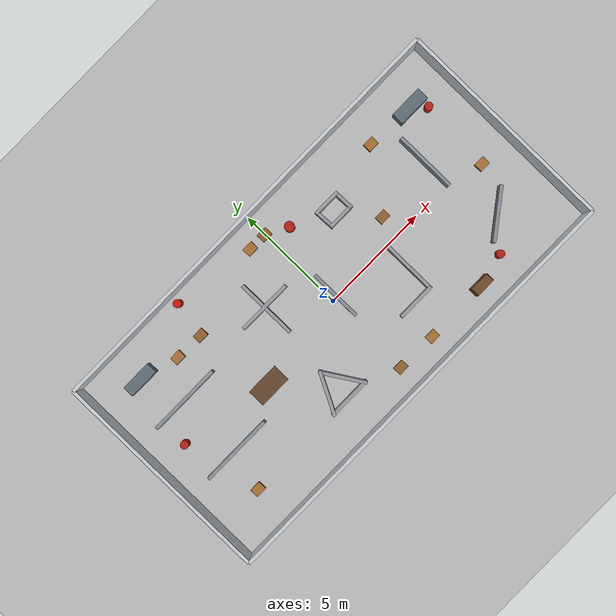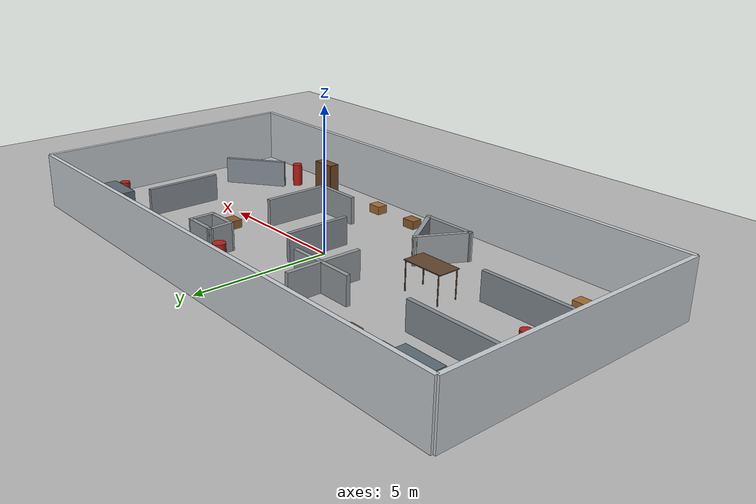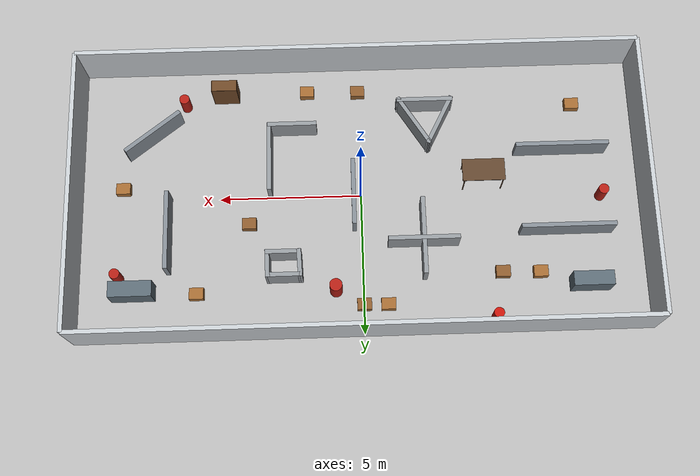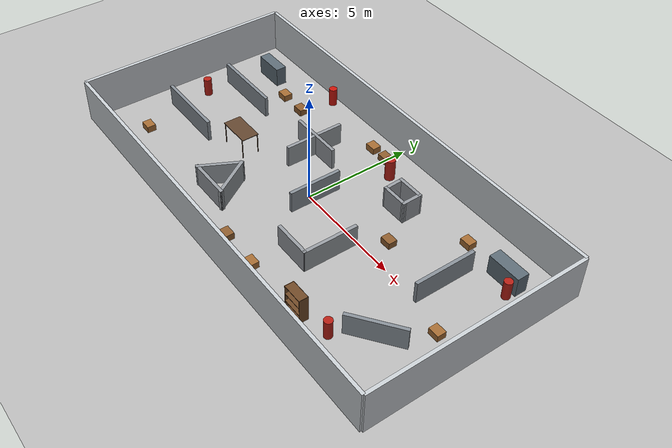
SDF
<?xml version='1.0'?>
<sdf version='1.6'>
  <world name='default'>
    <plugin name='gazebo_ros_state' filename='libgazebo_ros_state.so'>
      <update_rate>30.0</update_rate>
    </plugin>
    <light name='sun' type='directional'>
      <cast_shadows>1</cast_shadows>
      <pose>0 0 10 0 0 0</pose>
      <diffuse>0.8 0.8 0.8 1</diffuse>
      <specular>0.1 0.1 0.1 1</specular>
      <attenuation>
        <range>1000</range>
        <constant>0.9</constant>
        <linear>0.01</linear>
        <quadratic>0.001</quadratic>
      </attenuation>
      <direction>-0.5 0.5 -1</direction>
    </light>
    <model name='ground_plane'>
      <static>true</static>
      <link name='link'>
        <collision name='collision'>
          <geometry><plane><normal>0 0 1</normal><size>100 100</size></plane></geometry>
          <surface>
            <friction>
              <ode>
                <mu>100</mu>
                <mu2>50</mu2>
              </ode>
              <torsional>
                <ode/>
              </torsional>
            </friction>
            <contact>
              <ode/>
            </contact>
            <bounce/>
          </surface>
          <max_contacts>10</max_contacts>
        </collision>
        <visual name='visual'>
          <cast_shadows>false</cast_shadows>
          <geometry><plane><normal>0 0 1</normal><size>100 100</size></plane></geometry>
          <material>
            <ambient>0.72 0.72 0.72 1</ambient>
            <diffuse>0.72 0.72 0.72 1</diffuse>
          </material>
        </visual>
        <self_collide>0</self_collide>
        <kinematic>0</kinematic>
        <gravity>1</gravity>
      </link>
    </model>
    <gravity>0 0 -9.8</gravity>
    <magnetic_field>6e-06 2.3e-05 -4.2e-05</magnetic_field>
    <atmosphere type='adiabatic'/>
    <physics name='default_physics' default='0' type='ode'>
      <max_step_size>0.001</max_step_size>
      <real_time_factor>1</real_time_factor>
      <real_time_update_rate>1000</real_time_update_rate>
    </physics>
    <scene>
      <ambient>0.4 0.4 0.4 1</ambient>
      <background>0.7 0.7 0.7 1</background>
      <shadows>1</shadows>
    </scene>
    <gui fullscreen='0'>
      <camera name='user_camera'>
        <pose>0 0 22 0 1.57079632679 0</pose>
        <view_controller>orbit</view_controller>
        <projection_type>perspective</projection_type>
      </camera>
    </gui>
    <spherical_coordinates>
      <surface_model>EARTH_WGS84</surface_model>
      <latitude_deg>0</latitude_deg>
      <longitude_deg>0</longitude_deg>
      <elevation>0</elevation>
      <heading_deg>0</heading_deg>
    </spherical_coordinates>
    <model name='boundary_wall_north'>
      <static>true</static>
      <pose>0 5 1 0 0 0</pose>
      <link name='link'>
        <collision name='collision'>
          <geometry>
            <box>
              <size>20 0.15 2</size>
            </box>
          </geometry>
          <surface>
            <friction>
              <ode>
                <mu>1</mu>
                <mu2>1</mu2>
                <fdir1>0 0 0</fdir1>
                <slip1>0</slip1>
                <slip2>0</slip2>
              </ode>
              <torsional>
                <coefficient>1</coefficient>
                <patch_radius>0</patch_radius>
                <surface_radius>0</surface_radius>
                <use_patch_radius>1</use_patch_radius>
                <ode>
                  <slip>0</slip>
                </ode>
              </torsional>
            </friction>
            <bounce>
              <restitution_coefficient>0</restitution_coefficient>
              <threshold>1e+06</threshold>
            </bounce>
            <contact>
              <collide_without_contact>0</collide_without_contact>
              <collide_without_contact_bitmask>1</collide_without_contact_bitmask>
              <collide_bitmask>1</collide_bitmask>
              <ode>
                <soft_cfm>0</soft_cfm>
                <soft_erp>0.2</soft_erp>
                <kp>1e+13</kp>
                <kd>1</kd>
                <max_vel>0.01</max_vel>
                <min_depth>0</min_depth>
              </ode>
              <bullet>
                <split_impulse>1</split_impulse>
                <split_impulse_penetration_threshold>-0.01</split_impulse_penetration_threshold>
                <soft_cfm>0</soft_cfm>
                <soft_erp>0.2</soft_erp>
                <kp>1e+13</kp>
                <kd>1</kd>
              </bullet>
            </contact>
          </surface>
          <max_contacts>10</max_contacts>
        </collision>
        <visual name='visual'>
          <geometry>
            <box>
              <size>20 0.15 2</size>
            </box>
          </geometry>
              <material>
                <ambient>0.78 0.8 0.82 1</ambient>
                <diffuse>0.78 0.8 0.82 1</diffuse>
              </material>
        </visual>
      </link>
    </model>
    <model name='boundary_wall_south'>
      <static>true</static>
      <pose>0 -5 1 0 0 3.1415927</pose>
      <link name='link'>
        <collision name='collision'>
          <geometry>
            <box>
              <size>20 0.15 2</size>
            </box>
          </geometry>
          <surface>
            <friction>
              <ode>
                <mu>1</mu>
                <mu2>1</mu2>
                <fdir1>0 0 0</fdir1>
                <slip1>0</slip1>
                <slip2>0</slip2>
              </ode>
              <torsional>
                <coefficient>1</coefficient>
                <patch_radius>0</patch_radius>
                <surface_radius>0</surface_radius>
                <use_patch_radius>1</use_patch_radius>
                <ode>
                  <slip>0</slip>
                </ode>
              </torsional>
            </friction>
            <bounce>
              <restitution_coefficient>0</restitution_coefficient>
              <threshold>1e+06</threshold>
            </bounce>
            <contact>
              <collide_without_contact>0</collide_without_contact>
              <collide_without_contact_bitmask>1</collide_without_contact_bitmask>
              <collide_bitmask>1</collide_bitmask>
              <ode>
                <soft_cfm>0</soft_cfm>
                <soft_erp>0.2</soft_erp>
                <kp>1e+13</kp>
                <kd>1</kd>
                <max_vel>0.01</max_vel>
                <min_depth>0</min_depth>
              </ode>
              <bullet>
                <split_impulse>1</split_impulse>
                <split_impulse_penetration_threshold>-0.01</split_impulse_penetration_threshold>
                <soft_cfm>0</soft_cfm>
                <soft_erp>0.2</soft_erp>
                <kp>1e+13</kp>
                <kd>1</kd>
              </bullet>
            </contact>
          </surface>
          <max_contacts>10</max_contacts>
        </collision>
        <visual name='visual'>
          <geometry>
            <box>
              <size>20 0.15 2</size>
            </box>
          </geometry>
              <material>
                <ambient>0.78 0.8 0.82 1</ambient>
                <diffuse>0.78 0.8 0.82 1</diffuse>
              </material>
        </visual>
      </link>
    </model>
    <model name='boundary_wall_east'>
      <static>true</static>
      <pose>10 0 1 0 0 -1.5707963</pose>
      <link name='link'>
        <collision name='collision'>
          <geometry>
            <box>
              <size>10 0.15 2</size>
            </box>
          </geometry>
          <surface>
            <friction>
              <ode>
                <mu>1</mu>
                <mu2>1</mu2>
                <fdir1>0 0 0</fdir1>
                <slip1>0</slip1>
                <slip2>0</slip2>
              </ode>
              <torsional>
                <coefficient>1</coefficient>
                <patch_radius>0</patch_radius>
                <surface_radius>0</surface_radius>
                <use_patch_radius>1</use_patch_radius>
                <ode>
                  <slip>0</slip>
                </ode>
              </torsional>
            </friction>
            <bounce>
              <restitution_coefficient>0</restitution_coefficient>
              <threshold>1e+06</threshold>
            </bounce>
            <contact>
              <collide_without_contact>0</collide_without_contact>
              <collide_without_contact_bitmask>1</collide_without_contact_bitmask>
              <collide_bitmask>1</collide_bitmask>
              <ode>
                <soft_cfm>0</soft_cfm>
                <soft_erp>0.2</soft_erp>
                <kp>1e+13</kp>
                <kd>1</kd>
                <max_vel>0.01</max_vel>
                <min_depth>0</min_depth>
              </ode>
              <bullet>
                <split_impulse>1</split_impulse>
                <split_impulse_penetration_threshold>-0.01</split_impulse_penetration_threshold>
                <soft_cfm>0</soft_cfm>
                <soft_erp>0.2</soft_erp>
                <kp>1e+13</kp>
                <kd>1</kd>
              </bullet>
            </contact>
          </surface>
          <max_contacts>10</max_contacts>
        </collision>
        <visual name='visual'>
          <geometry>
            <box>
              <size>10 0.15 2</size>
            </box>
          </geometry>
              <material>
                <ambient>0.78 0.8 0.82 1</ambient>
                <diffuse>0.78 0.8 0.82 1</diffuse>
              </material>
        </visual>
      </link>
    </model>
    <model name='boundary_wall_west'>
      <static>true</static>
      <pose>-10 0 1 0 0 1.5707963</pose>
      <link name='link'>
        <collision name='collision'>
          <geometry>
            <box>
              <size>10 0.15 2</size>
            </box>
          </geometry>
          <surface>
            <friction>
              <ode>
                <mu>1</mu>
                <mu2>1</mu2>
                <fdir1>0 0 0</fdir1>
                <slip1>0</slip1>
                <slip2>0</slip2>
              </ode>
              <torsional>
                <coefficient>1</coefficient>
                <patch_radius>0</patch_radius>
                <surface_radius>0</surface_radius>
                <use_patch_radius>1</use_patch_radius>
                <ode>
                  <slip>0</slip>
                </ode>
              </torsional>
            </friction>
            <bounce>
              <restitution_coefficient>0</restitution_coefficient>
              <threshold>1e+06</threshold>
            </bounce>
            <contact>
              <collide_without_contact>0</collide_without_contact>
              <collide_without_contact_bitmask>1</collide_without_contact_bitmask>
              <collide_bitmask>1</collide_bitmask>
              <ode>
                <soft_cfm>0</soft_cfm>
                <soft_erp>0.2</soft_erp>
                <kp>1e+13</kp>
                <kd>1</kd>
                <max_vel>0.01</max_vel>
                <min_depth>0</min_depth>
              </ode>
              <bullet>
                <split_impulse>1</split_impulse>
                <split_impulse_penetration_threshold>-0.01</split_impulse_penetration_threshold>
                <soft_cfm>0</soft_cfm>
                <soft_erp>0.2</soft_erp>
                <kp>1e+13</kp>
                <kd>1</kd>
              </bullet>
            </contact>
          </surface>
          <max_contacts>10</max_contacts>
        </collision>
        <visual name='visual'>
          <geometry>
            <box>
              <size>10 0.15 2</size>
            </box>
          </geometry>
              <material>
                <ambient>0.78 0.8 0.82 1</ambient>
                <diffuse>0.78 0.8 0.82 1</diffuse>
              </material>
        </visual>
      </link>
    </model>
    <model name='bookshelf_link_back'>
      <static>true</static>
      <pose>4.78412 -3.73336 0.6 0 0 0</pose>
      <link name='link'>
        <collision name='collision'>
          <geometry>
            <box>
              <size>0.9 0.01 1.2</size>
            </box>
          </geometry>
          <surface>
            <friction>
              <ode>
                <mu>1</mu>
                <mu2>1</mu2>
                <fdir1>0 0 0</fdir1>
                <slip1>0</slip1>
                <slip2>0</slip2>
              </ode>
              <torsional>
                <coefficient>1</coefficient>
                <patch_radius>0</patch_radius>
                <surface_radius>0</surface_radius>
                <use_patch_radius>1</use_patch_radius>
                <ode>
                  <slip>0</slip>
                </ode>
              </torsional>
            </friction>
            <bounce>
              <restitution_coefficient>0</restitution_coefficient>
              <threshold>1e+06</threshold>
            </bounce>
            <contact>
              <collide_without_contact>0</collide_without_contact>
              <collide_without_contact_bitmask>1</collide_without_contact_bitmask>
              <collide_bitmask>1</collide_bitmask>
              <ode>
                <soft_cfm>0</soft_cfm>
                <soft_erp>0.2</soft_erp>
                <kp>1e+13</kp>
                <kd>1</kd>
                <max_vel>0.01</max_vel>
                <min_depth>0</min_depth>
              </ode>
              <bullet>
                <split_impulse>1</split_impulse>
                <split_impulse_penetration_threshold>-0.01</split_impulse_penetration_threshold>
                <soft_cfm>0</soft_cfm>
                <soft_erp>0.2</soft_erp>
                <kp>1e+13</kp>
                <kd>1</kd>
              </bullet>
            </contact>
          </surface>
          <max_contacts>10</max_contacts>
        </collision>
        <visual name='visual'>
          <geometry>
            <box>
              <size>0.9 0.01 1.2</size>
            </box>
          </geometry>
              <material>
                <ambient>0.43 0.28 0.15 1</ambient>
                <diffuse>0.43 0.28 0.15 1</diffuse>
              </material>
        </visual>
      </link>
    </model>
    <model name='bookshelf_link_bottom'>
      <static>true</static>
      <pose>4.78412 -3.93336 0.03 0 0 0</pose>
      <link name='link'>
        <collision name='collision'>
          <geometry>
            <box>
              <size>0.88 0.4 0.06</size>
            </box>
          </geometry>
          <surface>
            <friction>
              <ode>
                <mu>1</mu>
                <mu2>1</mu2>
                <fdir1>0 0 0</fdir1>
                <slip1>0</slip1>
                <slip2>0</slip2>
              </ode>
              <torsional>
                <coefficient>1</coefficient>
                <patch_radius>0</patch_radius>
                <surface_radius>0</surface_radius>
                <use_patch_radius>1</use_patch_radius>
                <ode>
                  <slip>0</slip>
                </ode>
              </torsional>
            </friction>
            <bounce>
              <restitution_coefficient>0</restitution_coefficient>
              <threshold>1e+06</threshold>
            </bounce>
            <contact>
              <collide_without_contact>0</collide_without_contact>
              <collide_without_contact_bitmask>1</collide_without_contact_bitmask>
              <collide_bitmask>1</collide_bitmask>
              <ode>
                <soft_cfm>0</soft_cfm>
                <soft_erp>0.2</soft_erp>
                <kp>1e+13</kp>
                <kd>1</kd>
                <max_vel>0.01</max_vel>
                <min_depth>0</min_depth>
              </ode>
              <bullet>
                <split_impulse>1</split_impulse>
                <split_impulse_penetration_threshold>-0.01</split_impulse_penetration_threshold>
                <soft_cfm>0</soft_cfm>
                <soft_erp>0.2</soft_erp>
                <kp>1e+13</kp>
                <kd>1</kd>
              </bullet>
            </contact>
          </surface>
          <max_contacts>10</max_contacts>
        </collision>
        <visual name='visual'>
          <geometry>
            <box>
              <size>0.88 0.4 0.06</size>
            </box>
          </geometry>
              <material>
                <ambient>0.43 0.28 0.15 1</ambient>
                <diffuse>0.43 0.28 0.15 1</diffuse>
              </material>
        </visual>
      </link>
    </model>
    <model name='bookshelf_link_high_shelf'>
      <static>true</static>
      <pose>4.78412 -3.93336 0.8 0 0 0</pose>
      <link name='link'>
        <collision name='collision'>
          <geometry>
            <box>
              <size>0.88 0.4 0.02</size>
            </box>
          </geometry>
          <surface>
            <friction>
              <ode>
                <mu>1</mu>
                <mu2>1</mu2>
                <fdir1>0 0 0</fdir1>
                <slip1>0</slip1>
                <slip2>0</slip2>
              </ode>
              <torsional>
                <coefficient>1</coefficient>
                <patch_radius>0</patch_radius>
                <surface_radius>0</surface_radius>
                <use_patch_radius>1</use_patch_radius>
                <ode>
                  <slip>0</slip>
                </ode>
              </torsional>
            </friction>
            <bounce>
              <restitution_coefficient>0</restitution_coefficient>
              <threshold>1e+06</threshold>
            </bounce>
            <contact>
              <collide_without_contact>0</collide_without_contact>
              <collide_without_contact_bitmask>1</collide_without_contact_bitmask>
              <collide_bitmask>1</collide_bitmask>
              <ode>
                <soft_cfm>0</soft_cfm>
                <soft_erp>0.2</soft_erp>
                <kp>1e+13</kp>
                <kd>1</kd>
                <max_vel>0.01</max_vel>
                <min_depth>0</min_depth>
              </ode>
              <bullet>
                <split_impulse>1</split_impulse>
                <split_impulse_penetration_threshold>-0.01</split_impulse_penetration_threshold>
                <soft_cfm>0</soft_cfm>
                <soft_erp>0.2</soft_erp>
                <kp>1e+13</kp>
                <kd>1</kd>
              </bullet>
            </contact>
          </surface>
          <max_contacts>10</max_contacts>
        </collision>
        <visual name='visual'>
          <geometry>
            <box>
              <size>0.88 0.4 0.02</size>
            </box>
          </geometry>
              <material>
                <ambient>0.43 0.28 0.15 1</ambient>
                <diffuse>0.43 0.28 0.15 1</diffuse>
              </material>
        </visual>
      </link>
    </model>
    <model name='bookshelf_link_left_side'>
      <static>true</static>
      <pose>5.23412 -3.93336 0.6 0 0 0</pose>
      <link name='link'>
        <collision name='collision'>
          <geometry>
            <box>
              <size>0.02 0.4 1.2</size>
            </box>
          </geometry>
          <surface>
            <friction>
              <ode>
                <mu>1</mu>
                <mu2>1</mu2>
                <fdir1>0 0 0</fdir1>
                <slip1>0</slip1>
                <slip2>0</slip2>
              </ode>
              <torsional>
                <coefficient>1</coefficient>
                <patch_radius>0</patch_radius>
                <surface_radius>0</surface_radius>
                <use_patch_radius>1</use_patch_radius>
                <ode>
                  <slip>0</slip>
                </ode>
              </torsional>
            </friction>
            <bounce>
              <restitution_coefficient>0</restitution_coefficient>
              <threshold>1e+06</threshold>
            </bounce>
            <contact>
              <collide_without_contact>0</collide_without_contact>
              <collide_without_contact_bitmask>1</collide_without_contact_bitmask>
              <collide_bitmask>1</collide_bitmask>
              <ode>
                <soft_cfm>0</soft_cfm>
                <soft_erp>0.2</soft_erp>
                <kp>1e+13</kp>
                <kd>1</kd>
                <max_vel>0.01</max_vel>
                <min_depth>0</min_depth>
              </ode>
              <bullet>
                <split_impulse>1</split_impulse>
                <split_impulse_penetration_threshold>-0.01</split_impulse_penetration_threshold>
                <soft_cfm>0</soft_cfm>
                <soft_erp>0.2</soft_erp>
                <kp>1e+13</kp>
                <kd>1</kd>
              </bullet>
            </contact>
          </surface>
          <max_contacts>10</max_contacts>
        </collision>
        <visual name='visual'>
          <geometry>
            <box>
              <size>0.02 0.4 1.2</size>
            </box>
          </geometry>
              <material>
                <ambient>0.43 0.28 0.15 1</ambient>
                <diffuse>0.43 0.28 0.15 1</diffuse>
              </material>
        </visual>
      </link>
    </model>
    <model name='bookshelf_link_low_shelf'>
      <static>true</static>
      <pose>4.78412 -3.93336 0.43 0 0 0</pose>
      <link name='link'>
        <collision name='collision'>
          <geometry>
            <box>
              <size>0.88 0.4 0.02</size>
            </box>
          </geometry>
          <surface>
            <friction>
              <ode>
                <mu>1</mu>
                <mu2>1</mu2>
                <fdir1>0 0 0</fdir1>
                <slip1>0</slip1>
                <slip2>0</slip2>
              </ode>
              <torsional>
                <coefficient>1</coefficient>
                <patch_radius>0</patch_radius>
                <surface_radius>0</surface_radius>
                <use_patch_radius>1</use_patch_radius>
                <ode>
                  <slip>0</slip>
                </ode>
              </torsional>
            </friction>
            <bounce>
              <restitution_coefficient>0</restitution_coefficient>
              <threshold>1e+06</threshold>
            </bounce>
            <contact>
              <collide_without_contact>0</collide_without_contact>
              <collide_without_contact_bitmask>1</collide_without_contact_bitmask>
              <collide_bitmask>1</collide_bitmask>
              <ode>
                <soft_cfm>0</soft_cfm>
                <soft_erp>0.2</soft_erp>
                <kp>1e+13</kp>
                <kd>1</kd>
                <max_vel>0.01</max_vel>
                <min_depth>0</min_depth>
              </ode>
              <bullet>
                <split_impulse>1</split_impulse>
                <split_impulse_penetration_threshold>-0.01</split_impulse_penetration_threshold>
                <soft_cfm>0</soft_cfm>
                <soft_erp>0.2</soft_erp>
                <kp>1e+13</kp>
                <kd>1</kd>
              </bullet>
            </contact>
          </surface>
          <max_contacts>10</max_contacts>
        </collision>
        <visual name='visual'>
          <geometry>
            <box>
              <size>0.88 0.4 0.02</size>
            </box>
          </geometry>
              <material>
                <ambient>0.43 0.28 0.15 1</ambient>
                <diffuse>0.43 0.28 0.15 1</diffuse>
              </material>
        </visual>
      </link>
    </model>
    <model name='bookshelf_link_right_side'>
      <static>true</static>
      <pose>4.33412 -3.93336 0.6 0 0 0</pose>
      <link name='link'>
        <collision name='collision'>
          <geometry>
            <box>
              <size>0.02 0.4 1.2</size>
            </box>
          </geometry>
          <surface>
            <friction>
              <ode>
                <mu>1</mu>
                <mu2>1</mu2>
                <fdir1>0 0 0</fdir1>
                <slip1>0</slip1>
                <slip2>0</slip2>
              </ode>
              <torsional>
                <coefficient>1</coefficient>
                <patch_radius>0</patch_radius>
                <surface_radius>0</surface_radius>
                <use_patch_radius>1</use_patch_radius>
                <ode>
                  <slip>0</slip>
                </ode>
              </torsional>
            </friction>
            <bounce>
              <restitution_coefficient>0</restitution_coefficient>
              <threshold>1e+06</threshold>
            </bounce>
            <contact>
              <collide_without_contact>0</collide_without_contact>
              <collide_without_contact_bitmask>1</collide_without_contact_bitmask>
              <collide_bitmask>1</collide_bitmask>
              <ode>
                <soft_cfm>0</soft_cfm>
                <soft_erp>0.2</soft_erp>
                <kp>1e+13</kp>
                <kd>1</kd>
                <max_vel>0.01</max_vel>
                <min_depth>0</min_depth>
              </ode>
              <bullet>
                <split_impulse>1</split_impulse>
                <split_impulse_penetration_threshold>-0.01</split_impulse_penetration_threshold>
                <soft_cfm>0</soft_cfm>
                <soft_erp>0.2</soft_erp>
                <kp>1e+13</kp>
                <kd>1</kd>
              </bullet>
            </contact>
          </surface>
          <max_contacts>10</max_contacts>
        </collision>
        <visual name='visual'>
          <geometry>
            <box>
              <size>0.02 0.4 1.2</size>
            </box>
          </geometry>
              <material>
                <ambient>0.43 0.28 0.15 1</ambient>
                <diffuse>0.43 0.28 0.15 1</diffuse>
              </material>
        </visual>
      </link>
    </model>
    <model name='bookshelf_link_top'>
      <static>true</static>
      <pose>4.78412 -3.93336 1.19 0 0 0</pose>
      <link name='link'>
        <collision name='collision'>
          <geometry>
            <box>
              <size>0.88 0.4 0.02</size>
            </box>
          </geometry>
          <surface>
            <friction>
              <ode>
                <mu>1</mu>
                <mu2>1</mu2>
                <fdir1>0 0 0</fdir1>
                <slip1>0</slip1>
                <slip2>0</slip2>
              </ode>
              <torsional>
                <coefficient>1</coefficient>
                <patch_radius>0</patch_radius>
                <surface_radius>0</surface_radius>
                <use_patch_radius>1</use_patch_radius>
                <ode>
                  <slip>0</slip>
                </ode>
              </torsional>
            </friction>
            <bounce>
              <restitution_coefficient>0</restitution_coefficient>
              <threshold>1e+06</threshold>
            </bounce>
            <contact>
              <collide_without_contact>0</collide_without_contact>
              <collide_without_contact_bitmask>1</collide_without_contact_bitmask>
              <collide_bitmask>1</collide_bitmask>
              <ode>
                <soft_cfm>0</soft_cfm>
                <soft_erp>0.2</soft_erp>
                <kp>1e+13</kp>
                <kd>1</kd>
                <max_vel>0.01</max_vel>
                <min_depth>0</min_depth>
              </ode>
              <bullet>
                <split_impulse>1</split_impulse>
                <split_impulse_penetration_threshold>-0.01</split_impulse_penetration_threshold>
                <soft_cfm>0</soft_cfm>
                <soft_erp>0.2</soft_erp>
                <kp>1e+13</kp>
                <kd>1</kd>
              </bullet>
            </contact>
          </surface>
          <max_contacts>10</max_contacts>
        </collision>
        <visual name='visual'>
          <geometry>
            <box>
              <size>0.88 0.4 0.02</size>
            </box>
          </geometry>
              <material>
                <ambient>0.43 0.28 0.15 1</ambient>
                <diffuse>0.43 0.28 0.15 1</diffuse>
              </material>
        </visual>
      </link>
    </model>
    <model name='box_Wall_11_Wall_11_Collision'>
      <static>true</static>
      <pose>-2.15144 1.85688 0.5 0 0 0</pose>
      <link name='link'>
        <collision name='collision'>
          <geometry>
            <box>
              <size>2.5 0.15 1</size>
            </box>
          </geometry>
          <surface>
            <friction>
              <ode>
                <mu>1</mu>
                <mu2>1</mu2>
                <fdir1>0 0 0</fdir1>
                <slip1>0</slip1>
                <slip2>0</slip2>
              </ode>
              <torsional>
                <coefficient>1</coefficient>
                <patch_radius>0</patch_radius>
                <surface_radius>0</surface_radius>
                <use_patch_radius>1</use_patch_radius>
                <ode>
                  <slip>0</slip>
                </ode>
              </torsional>
            </friction>
            <bounce>
              <restitution_coefficient>0</restitution_coefficient>
              <threshold>1e+06</threshold>
            </bounce>
            <contact>
              <collide_without_contact>0</collide_without_contact>
              <collide_without_contact_bitmask>1</collide_without_contact_bitmask>
              <collide_bitmask>1</collide_bitmask>
              <ode>
                <soft_cfm>0</soft_cfm>
                <soft_erp>0.2</soft_erp>
                <kp>1e+13</kp>
                <kd>1</kd>
                <max_vel>0.01</max_vel>
                <min_depth>0</min_depth>
              </ode>
              <bullet>
                <split_impulse>1</split_impulse>
                <split_impulse_penetration_threshold>-0.01</split_impulse_penetration_threshold>
                <soft_cfm>0</soft_cfm>
                <soft_erp>0.2</soft_erp>
                <kp>1e+13</kp>
                <kd>1</kd>
              </bullet>
            </contact>
          </surface>
          <max_contacts>10</max_contacts>
        </collision>
        <visual name='visual'>
          <geometry>
            <box>
              <size>2.5 0.15 1</size>
            </box>
          </geometry>
              <material>
                <ambient>0.58 0.6 0.62 1</ambient>
                <diffuse>0.58 0.6 0.62 1</diffuse>
              </material>
        </visual>
      </link>
    </model>
    <model name='box_Wall_13_Wall_13_Collision'>
      <static>true</static>
      <pose>-2.15444 1.76388 0.5 0 0 -1.5708</pose>
      <link name='link'>
        <collision name='collision'>
          <geometry>
            <box>
              <size>2.75 0.15 1</size>
            </box>
          </geometry>
          <surface>
            <friction>
              <ode>
                <mu>1</mu>
                <mu2>1</mu2>
                <fdir1>0 0 0</fdir1>
                <slip1>0</slip1>
                <slip2>0</slip2>
              </ode>
              <torsional>
                <coefficient>1</coefficient>
                <patch_radius>0</patch_radius>
                <surface_radius>0</surface_radius>
                <use_patch_radius>1</use_patch_radius>
                <ode>
                  <slip>0</slip>
                </ode>
              </torsional>
            </friction>
            <bounce>
              <restitution_coefficient>0</restitution_coefficient>
              <threshold>1e+06</threshold>
            </bounce>
            <contact>
              <collide_without_contact>0</collide_without_contact>
              <collide_without_contact_bitmask>1</collide_without_contact_bitmask>
              <collide_bitmask>1</collide_bitmask>
              <ode>
                <soft_cfm>0</soft_cfm>
                <soft_erp>0.2</soft_erp>
                <kp>1e+13</kp>
                <kd>1</kd>
                <max_vel>0.01</max_vel>
                <min_depth>0</min_depth>
              </ode>
              <bullet>
                <split_impulse>1</split_impulse>
                <split_impulse_penetration_threshold>-0.01</split_impulse_penetration_threshold>
                <soft_cfm>0</soft_cfm>
                <soft_erp>0.2</soft_erp>
                <kp>1e+13</kp>
                <kd>1</kd>
              </bullet>
            </contact>
          </surface>
          <max_contacts>10</max_contacts>
        </collision>
        <visual name='visual'>
          <geometry>
            <box>
              <size>2.75 0.15 1</size>
            </box>
          </geometry>
              <material>
                <ambient>0.58 0.6 0.62 1</ambient>
                <diffuse>0.58 0.6 0.62 1</diffuse>
              </material>
        </visual>
      </link>
    </model>
    <model name='box_Wall_15_Wall_15_Collision'>
      <static>true</static>
      <pose>2.72456 3.02888 0.5 0 0 0</pose>
      <link name='link'>
        <collision name='collision'>
          <geometry>
            <box>
              <size>1.2678 0.15 1</size>
            </box>
          </geometry>
          <surface>
            <friction>
              <ode>
                <mu>1</mu>
                <mu2>1</mu2>
                <fdir1>0 0 0</fdir1>
                <slip1>0</slip1>
                <slip2>0</slip2>
              </ode>
              <torsional>
                <coefficient>1</coefficient>
                <patch_radius>0</patch_radius>
                <surface_radius>0</surface_radius>
                <use_patch_radius>1</use_patch_radius>
                <ode>
                  <slip>0</slip>
                </ode>
              </torsional>
            </friction>
            <bounce>
              <restitution_coefficient>0</restitution_coefficient>
              <threshold>1e+06</threshold>
            </bounce>
            <contact>
              <collide_without_contact>0</collide_without_contact>
              <collide_without_contact_bitmask>1</collide_without_contact_bitmask>
              <collide_bitmask>1</collide_bitmask>
              <ode>
                <soft_cfm>0</soft_cfm>
                <soft_erp>0.2</soft_erp>
                <kp>1e+13</kp>
                <kd>1</kd>
                <max_vel>0.01</max_vel>
                <min_depth>0</min_depth>
              </ode>
              <bullet>
                <split_impulse>1</split_impulse>
                <split_impulse_penetration_threshold>-0.01</split_impulse_penetration_threshold>
                <soft_cfm>0</soft_cfm>
                <soft_erp>0.2</soft_erp>
                <kp>1e+13</kp>
                <kd>1</kd>
              </bullet>
            </contact>
          </surface>
          <max_contacts>10</max_contacts>
        </collision>
        <visual name='visual'>
          <geometry>
            <box>
              <size>1.2678 0.15 1</size>
            </box>
          </geometry>
              <material>
                <ambient>0.58 0.6 0.62 1</ambient>
                <diffuse>0.58 0.6 0.62 1</diffuse>
              </material>
        </visual>
      </link>
    </model>
    <model name='box_Wall_16_Wall_16_Collision'>
      <static>true</static>
      <pose>3.29206 2.62138 0.5 0 0 -1.54994</pose>
      <link name='link'>
        <collision name='collision'>
          <geometry>
            <box>
              <size>0.965005 0.15 1</size>
            </box>
          </geometry>
          <surface>
            <friction>
              <ode>
                <mu>1</mu>
                <mu2>1</mu2>
                <fdir1>0 0 0</fdir1>
                <slip1>0</slip1>
                <slip2>0</slip2>
              </ode>
              <torsional>
                <coefficient>1</coefficient>
                <patch_radius>0</patch_radius>
                <surface_radius>0</surface_radius>
                <use_patch_radius>1</use_patch_radius>
                <ode>
                  <slip>0</slip>
                </ode>
              </torsional>
            </friction>
            <bounce>
              <restitution_coefficient>0</restitution_coefficient>
              <threshold>1e+06</threshold>
            </bounce>
            <contact>
              <collide_without_contact>0</collide_without_contact>
              <collide_without_contact_bitmask>1</collide_without_contact_bitmask>
              <collide_bitmask>1</collide_bitmask>
              <ode>
                <soft_cfm>0</soft_cfm>
                <soft_erp>0.2</soft_erp>
                <kp>1e+13</kp>
                <kd>1</kd>
                <max_vel>0.01</max_vel>
                <min_depth>0</min_depth>
              </ode>
              <bullet>
                <split_impulse>1</split_impulse>
                <split_impulse_penetration_threshold>-0.01</split_impulse_penetration_threshold>
                <soft_cfm>0</soft_cfm>
                <soft_erp>0.2</soft_erp>
                <kp>1e+13</kp>
                <kd>1</kd>
              </bullet>
            </contact>
          </surface>
          <max_contacts>10</max_contacts>
        </collision>
        <visual name='visual'>
          <geometry>
            <box>
              <size>0.965005 0.15 1</size>
            </box>
          </geometry>
              <material>
                <ambient>0.58 0.6 0.62 1</ambient>
                <diffuse>0.58 0.6 0.62 1</diffuse>
              </material>
        </visual>
      </link>
    </model>
    <model name='box_Wall_17_Wall_17_Collision'>
      <static>true</static>
      <pose>2.75056 2.21388 0.5 0 0 3.14159</pose>
      <link name='link'>
        <collision name='collision'>
          <geometry>
            <box>
              <size>1.25 0.15 1</size>
            </box>
          </geometry>
          <surface>
            <friction>
              <ode>
                <mu>1</mu>
                <mu2>1</mu2>
                <fdir1>0 0 0</fdir1>
                <slip1>0</slip1>
                <slip2>0</slip2>
              </ode>
              <torsional>
                <coefficient>1</coefficient>
                <patch_radius>0</patch_radius>
                <surface_radius>0</surface_radius>
                <use_patch_radius>1</use_patch_radius>
                <ode>
                  <slip>0</slip>
                </ode>
              </torsional>
            </friction>
            <bounce>
              <restitution_coefficient>0</restitution_coefficient>
              <threshold>1e+06</threshold>
            </bounce>
            <contact>
              <collide_without_contact>0</collide_without_contact>
              <collide_without_contact_bitmask>1</collide_without_contact_bitmask>
              <collide_bitmask>1</collide_bitmask>
              <ode>
                <soft_cfm>0</soft_cfm>
                <soft_erp>0.2</soft_erp>
                <kp>1e+13</kp>
                <kd>1</kd>
                <max_vel>0.01</max_vel>
                <min_depth>0</min_depth>
              </ode>
              <bullet>
                <split_impulse>1</split_impulse>
                <split_impulse_penetration_threshold>-0.01</split_impulse_penetration_threshold>
                <soft_cfm>0</soft_cfm>
                <soft_erp>0.2</soft_erp>
                <kp>1e+13</kp>
                <kd>1</kd>
              </bullet>
            </contact>
          </surface>
          <max_contacts>10</max_contacts>
        </collision>
        <visual name='visual'>
          <geometry>
            <box>
              <size>1.25 0.15 1</size>
            </box>
          </geometry>
              <material>
                <ambient>0.58 0.6 0.62 1</ambient>
                <diffuse>0.58 0.6 0.62 1</diffuse>
              </material>
        </visual>
      </link>
    </model>
    <model name='box_Wall_18_Wall_18_Collision'>
      <static>true</static>
      <pose>2.18306 2.62138 0.5 0 0 1.61372</pose>
      <link name='link'>
        <collision name='collision'>
          <geometry>
            <box>
              <size>0.965005 0.15 1</size>
            </box>
          </geometry>
          <surface>
            <friction>
              <ode>
                <mu>1</mu>
                <mu2>1</mu2>
                <fdir1>0 0 0</fdir1>
                <slip1>0</slip1>
                <slip2>0</slip2>
              </ode>
              <torsional>
                <coefficient>1</coefficient>
                <patch_radius>0</patch_radius>
                <surface_radius>0</surface_radius>
                <use_patch_radius>1</use_patch_radius>
                <ode>
                  <slip>0</slip>
                </ode>
              </torsional>
            </friction>
            <bounce>
              <restitution_coefficient>0</restitution_coefficient>
              <threshold>1e+06</threshold>
            </bounce>
            <contact>
              <collide_without_contact>0</collide_without_contact>
              <collide_without_contact_bitmask>1</collide_without_contact_bitmask>
              <collide_bitmask>1</collide_bitmask>
              <ode>
                <soft_cfm>0</soft_cfm>
                <soft_erp>0.2</soft_erp>
                <kp>1e+13</kp>
                <kd>1</kd>
                <max_vel>0.01</max_vel>
                <min_depth>0</min_depth>
              </ode>
              <bullet>
                <split_impulse>1</split_impulse>
                <split_impulse_penetration_threshold>-0.01</split_impulse_penetration_threshold>
                <soft_cfm>0</soft_cfm>
                <soft_erp>0.2</soft_erp>
                <kp>1e+13</kp>
                <kd>1</kd>
              </bullet>
            </contact>
          </surface>
          <max_contacts>10</max_contacts>
        </collision>
        <visual name='visual'>
          <geometry>
            <box>
              <size>0.965005 0.15 1</size>
            </box>
          </geometry>
              <material>
                <ambient>0.58 0.6 0.62 1</ambient>
                <diffuse>0.58 0.6 0.62 1</diffuse>
              </material>
        </visual>
      </link>
    </model>
    <model name='box_Wall_24_Wall_24_Collision'>
      <static>true</static>
      <pose>-2.8952 -2.491 0.5 0 0 1.09459</pose>
      <link name='link'>
        <collision name='collision'>
          <geometry>
            <box>
              <size>1.97704 0.15 1</size>
            </box>
          </geometry>
          <surface>
            <friction>
              <ode>
                <mu>1</mu>
                <mu2>1</mu2>
                <fdir1>0 0 0</fdir1>
                <slip1>0</slip1>
                <slip2>0</slip2>
              </ode>
              <torsional>
                <coefficient>1</coefficient>
                <patch_radius>0</patch_radius>
                <surface_radius>0</surface_radius>
                <use_patch_radius>1</use_patch_radius>
                <ode>
                  <slip>0</slip>
                </ode>
              </torsional>
            </friction>
            <bounce>
              <restitution_coefficient>0</restitution_coefficient>
              <threshold>1e+06</threshold>
            </bounce>
            <contact>
              <collide_without_contact>0</collide_without_contact>
              <collide_without_contact_bitmask>1</collide_without_contact_bitmask>
              <collide_bitmask>1</collide_bitmask>
              <ode>
                <soft_cfm>0</soft_cfm>
                <soft_erp>0.2</soft_erp>
                <kp>1e+13</kp>
                <kd>1</kd>
                <max_vel>0.01</max_vel>
                <min_depth>0</min_depth>
              </ode>
              <bullet>
                <split_impulse>1</split_impulse>
                <split_impulse_penetration_threshold>-0.01</split_impulse_penetration_threshold>
                <soft_cfm>0</soft_cfm>
                <soft_erp>0.2</soft_erp>
                <kp>1e+13</kp>
                <kd>1</kd>
              </bullet>
            </contact>
          </surface>
          <max_contacts>10</max_contacts>
        </collision>
        <visual name='visual'>
          <geometry>
            <box>
              <size>1.97704 0.15 1</size>
            </box>
          </geometry>
              <material>
                <ambient>0.58 0.6 0.62 1</ambient>
                <diffuse>0.58 0.6 0.62 1</diffuse>
              </material>
        </visual>
      </link>
    </model>
    <model name='box_Wall_25_Wall_25_Collision'>
      <static>true</static>
      <pose>-1.97021 -2.491 0.5 0 0 -1.01325</pose>
      <link name='link'>
        <collision name='collision'>
          <geometry>
            <box>
              <size>2.06356 0.15 1</size>
            </box>
          </geometry>
          <surface>
            <friction>
              <ode>
                <mu>1</mu>
                <mu2>1</mu2>
                <fdir1>0 0 0</fdir1>
                <slip1>0</slip1>
                <slip2>0</slip2>
              </ode>
              <torsional>
                <coefficient>1</coefficient>
                <patch_radius>0</patch_radius>
                <surface_radius>0</surface_radius>
                <use_patch_radius>1</use_patch_radius>
                <ode>
                  <slip>0</slip>
                </ode>
              </torsional>
            </friction>
            <bounce>
              <restitution_coefficient>0</restitution_coefficient>
              <threshold>1e+06</threshold>
            </bounce>
            <contact>
              <collide_without_contact>0</collide_without_contact>
              <collide_without_contact_bitmask>1</collide_without_contact_bitmask>
              <collide_bitmask>1</collide_bitmask>
              <ode>
                <soft_cfm>0</soft_cfm>
                <soft_erp>0.2</soft_erp>
                <kp>1e+13</kp>
                <kd>1</kd>
                <max_vel>0.01</max_vel>
                <min_depth>0</min_depth>
              </ode>
              <bullet>
                <split_impulse>1</split_impulse>
                <split_impulse_penetration_threshold>-0.01</split_impulse_penetration_threshold>
                <soft_cfm>0</soft_cfm>
                <soft_erp>0.2</soft_erp>
                <kp>1e+13</kp>
                <kd>1</kd>
              </bullet>
            </contact>
          </surface>
          <max_contacts>10</max_contacts>
        </collision>
        <visual name='visual'>
          <geometry>
            <box>
              <size>2.06356 0.15 1</size>
            </box>
          </geometry>
              <material>
                <ambient>0.58 0.6 0.62 1</ambient>
                <diffuse>0.58 0.6 0.62 1</diffuse>
              </material>
        </visual>
      </link>
    </model>
    <model name='box_Wall_26_Wall_26_Collision'>
      <static>true</static>
      <pose>-2.38897 -3.28539 0.5 0 0 3.14159</pose>
      <link name='link'>
        <collision name='collision'>
          <geometry>
            <box>
              <size>2 0.15 1</size>
            </box>
          </geometry>
          <surface>
            <friction>
              <ode>
                <mu>1</mu>
                <mu2>1</mu2>
                <fdir1>0 0 0</fdir1>
                <slip1>0</slip1>
                <slip2>0</slip2>
              </ode>
              <torsional>
                <coefficient>1</coefficient>
                <patch_radius>0</patch_radius>
                <surface_radius>0</surface_radius>
                <use_patch_radius>1</use_patch_radius>
                <ode>
                  <slip>0</slip>
                </ode>
              </torsional>
            </friction>
            <bounce>
              <restitution_coefficient>0</restitution_coefficient>
              <threshold>1e+06</threshold>
            </bounce>
            <contact>
              <collide_without_contact>0</collide_without_contact>
              <collide_without_contact_bitmask>1</collide_without_contact_bitmask>
              <collide_bitmask>1</collide_bitmask>
              <ode>
                <soft_cfm>0</soft_cfm>
                <soft_erp>0.2</soft_erp>
                <kp>1e+13</kp>
                <kd>1</kd>
                <max_vel>0.01</max_vel>
                <min_depth>0</min_depth>
              </ode>
              <bullet>
                <split_impulse>1</split_impulse>
                <split_impulse_penetration_threshold>-0.01</split_impulse_penetration_threshold>
                <soft_cfm>0</soft_cfm>
                <soft_erp>0.2</soft_erp>
                <kp>1e+13</kp>
                <kd>1</kd>
              </bullet>
            </contact>
          </surface>
          <max_contacts>10</max_contacts>
        </collision>
        <visual name='visual'>
          <geometry>
            <box>
              <size>2 0.15 1</size>
            </box>
          </geometry>
              <material>
                <ambient>0.58 0.6 0.62 1</ambient>
                <diffuse>0.58 0.6 0.62 1</diffuse>
              </material>
        </visual>
      </link>
    </model>
    <model name='box_Wall_28_Wall_28_Collision'>
      <static>true</static>
      <pose>2.38869 -2.48059 0.5 0 0 0</pose>
      <link name='link'>
        <collision name='collision'>
          <geometry>
            <box>
              <size>1.75 0.15 1</size>
            </box>
          </geometry>
          <surface>
            <friction>
              <ode>
                <mu>1</mu>
                <mu2>1</mu2>
                <fdir1>0 0 0</fdir1>
                <slip1>0</slip1>
                <slip2>0</slip2>
              </ode>
              <torsional>
                <coefficient>1</coefficient>
                <patch_radius>0</patch_radius>
                <surface_radius>0</surface_radius>
                <use_patch_radius>1</use_patch_radius>
                <ode>
                  <slip>0</slip>
                </ode>
              </torsional>
            </friction>
            <bounce>
              <restitution_coefficient>0</restitution_coefficient>
              <threshold>1e+06</threshold>
            </bounce>
            <contact>
              <collide_without_contact>0</collide_without_contact>
              <collide_without_contact_bitmask>1</collide_without_contact_bitmask>
              <collide_bitmask>1</collide_bitmask>
              <ode>
                <soft_cfm>0</soft_cfm>
                <soft_erp>0.2</soft_erp>
                <kp>1e+13</kp>
                <kd>1</kd>
                <max_vel>0.01</max_vel>
                <min_depth>0</min_depth>
              </ode>
              <bullet>
                <split_impulse>1</split_impulse>
                <split_impulse_penetration_threshold>-0.01</split_impulse_penetration_threshold>
                <soft_cfm>0</soft_cfm>
                <soft_erp>0.2</soft_erp>
                <kp>1e+13</kp>
                <kd>1</kd>
              </bullet>
            </contact>
          </surface>
          <max_contacts>10</max_contacts>
        </collision>
        <visual name='visual'>
          <geometry>
            <box>
              <size>1.75 0.15 1</size>
            </box>
          </geometry>
              <material>
                <ambient>0.58 0.6 0.62 1</ambient>
                <diffuse>0.58 0.6 0.62 1</diffuse>
              </material>
        </visual>
      </link>
    </model>
    <model name='box_Wall_29_Wall_29_Collision'>
      <static>true</static>
      <pose>3.20618 -1.2881 0.5 0 0 1.5708</pose>
      <link name='link'>
        <collision name='collision'>
          <geometry>
            <box>
              <size>2.5 0.15 1</size>
            </box>
          </geometry>
          <surface>
            <friction>
              <ode>
                <mu>1</mu>
                <mu2>1</mu2>
                <fdir1>0 0 0</fdir1>
                <slip1>0</slip1>
                <slip2>0</slip2>
              </ode>
              <torsional>
                <coefficient>1</coefficient>
                <patch_radius>0</patch_radius>
                <surface_radius>0</surface_radius>
                <use_patch_radius>1</use_patch_radius>
                <ode>
                  <slip>0</slip>
                </ode>
              </torsional>
            </friction>
            <bounce>
              <restitution_coefficient>0</restitution_coefficient>
              <threshold>1e+06</threshold>
            </bounce>
            <contact>
              <collide_without_contact>0</collide_without_contact>
              <collide_without_contact_bitmask>1</collide_without_contact_bitmask>
              <collide_bitmask>1</collide_bitmask>
              <ode>
                <soft_cfm>0</soft_cfm>
                <soft_erp>0.2</soft_erp>
                <kp>1e+13</kp>
                <kd>1</kd>
                <max_vel>0.01</max_vel>
                <min_depth>0</min_depth>
              </ode>
              <bullet>
                <split_impulse>1</split_impulse>
                <split_impulse_penetration_threshold>-0.01</split_impulse_penetration_threshold>
                <soft_cfm>0</soft_cfm>
                <soft_erp>0.2</soft_erp>
                <kp>1e+13</kp>
                <kd>1</kd>
              </bullet>
            </contact>
          </surface>
          <max_contacts>10</max_contacts>
        </collision>
        <visual name='visual'>
          <geometry>
            <box>
              <size>2.5 0.15 1</size>
            </box>
          </geometry>
              <material>
                <ambient>0.58 0.6 0.62 1</ambient>
                <diffuse>0.58 0.6 0.62 1</diffuse>
              </material>
        </visual>
      </link>
    </model>
    <model name='cardboard_box_0'>
      <static>true</static>
      <pose>3.96847 0.977565 0.15 0 0 0</pose>
      <link name='link'>
        <collision name='collision'>
          <geometry>
            <box>
              <size>0.5 0.4 0.3</size>
            </box>
          </geometry>
          <surface>
            <friction>
              <ode>
                <mu>1</mu>
                <mu2>1</mu2>
              </ode>
              <torsional>
                <ode/>
              </torsional>
            </friction>
            <contact>
              <ode>
                <kp>1e+07</kp>
                <kd>1</kd>
                <min_depth>0.001</min_depth>
                <max_vel>0.1</max_vel>
              </ode>
            </contact>
            <bounce/>
          </surface>
          <max_contacts>10</max_contacts>
        </collision>
        <visual name='visual'>
          <geometry>
            <box>
              <size>0.5 0.4 0.3</size>
            </box>
          </geometry>
              <material>
                <ambient>0.55 0.36 0.18 1</ambient>
                <diffuse>0.55 0.36 0.18 1</diffuse>
              </material>
        </visual>
      </link>
    </model>
    <model name='cardboard_box_1'>
      <static>true</static>
      <pose>0.006438 -3.96264 0.15 0 0 0</pose>
      <link name='link'>
        <collision name='collision'>
          <geometry>
            <box>
              <size>0.5 0.4 0.3</size>
            </box>
          </geometry>
          <surface>
            <friction>
              <ode>
                <mu>1</mu>
                <mu2>1</mu2>
              </ode>
              <torsional>
                <ode/>
              </torsional>
            </friction>
            <contact>
              <ode>
                <kp>1e+07</kp>
                <kd>1</kd>
                <min_depth>0.001</min_depth>
                <max_vel>0.1</max_vel>
              </ode>
            </contact>
            <bounce/>
          </surface>
          <max_contacts>10</max_contacts>
        </collision>
        <visual name='visual'>
          <geometry>
            <box>
              <size>0.5 0.4 0.3</size>
            </box>
          </geometry>
              <material>
                <ambient>0.55 0.36 0.18 1</ambient>
                <diffuse>0.55 0.36 0.18 1</diffuse>
              </material>
        </visual>
      </link>
    </model>
    <model name='cardboard_box_2'>
      <static>true</static>
      <pose>-4.88373 2.96722 0.15 0 0 0</pose>
      <link name='link'>
        <collision name='collision'>
          <geometry>
            <box>
              <size>0.5 0.4 0.3</size>
            </box>
          </geometry>
          <surface>
            <friction>
              <ode>
                <mu>1</mu>
                <mu2>1</mu2>
              </ode>
              <torsional>
                <ode/>
              </torsional>
            </friction>
            <contact>
              <ode>
                <kp>1e+07</kp>
                <kd>1</kd>
                <min_depth>0.001</min_depth>
                <max_vel>0.1</max_vel>
              </ode>
            </contact>
            <bounce/>
          </surface>
          <max_contacts>10</max_contacts>
        </collision>
        <visual name='visual'>
          <geometry>
            <box>
              <size>0.5 0.4 0.3</size>
            </box>
          </geometry>
              <material>
                <ambient>0.55 0.36 0.18 1</ambient>
                <diffuse>0.55 0.36 0.18 1</diffuse>
              </material>
        </visual>
      </link>
    </model>
    <model name='cardboard_box_3'>
      <static>true</static>
      <pose>-0.0158 3.98725 0.15 0 0 0</pose>
      <link name='link'>
        <collision name='collision'>
          <geometry>
            <box>
              <size>0.5 0.4 0.3</size>
            </box>
          </geometry>
          <surface>
            <friction>
              <ode>
                <mu>1</mu>
                <mu2>1</mu2>
              </ode>
              <torsional>
                <ode/>
              </torsional>
            </friction>
            <contact>
              <ode>
                <kp>1e+07</kp>
                <kd>1</kd>
                <min_depth>0.001</min_depth>
                <max_vel>0.1</max_vel>
              </ode>
            </contact>
            <bounce/>
          </surface>
          <max_contacts>10</max_contacts>
        </collision>
        <visual name='visual'>
          <geometry>
            <box>
              <size>0.5 0.4 0.3</size>
            </box>
          </geometry>
              <material>
                <ambient>0.55 0.36 0.18 1</ambient>
                <diffuse>0.55 0.36 0.18 1</diffuse>
              </material>
        </visual>
      </link>
    </model>
    <model name='table_link_surface'>
      <static>true</static>
      <pose>-4.34248 -0.532954 1 0 0 0</pose>
      <link name='link'>
        <collision name='collision'>
          <geometry>
            <box>
              <size>1.5 0.8 0.03</size>
            </box>
          </geometry>
          <surface>
            <friction>
              <ode>
                <mu>0.6</mu>
                <mu2>0.6</mu2>
              </ode>
              <torsional>
                <ode/>
              </torsional>
            </friction>
            <contact>
              <ode/>
            </contact>
            <bounce/>
          </surface>
          <max_contacts>10</max_contacts>
        </collision>
        <visual name='visual'>
          <geometry>
            <box>
              <size>1.5 0.8 0.03</size>
            </box>
          </geometry>
              <material>
                <ambient>0.38 0.27 0.18 1</ambient>
                <diffuse>0.38 0.27 0.18 1</diffuse>
              </material>
        </visual>
      </link>
    </model>
    <model name='test_wall_left_corridor_upper'>
      <static>true</static>
      <pose>-7.2 1.55 0.5 0 0 0</pose>
      <link name='link'>
        <collision name='collision'>
          <geometry>
            <box>
              <size>3.3 0.15 1</size>
            </box>
          </geometry>
          <surface>
            <friction>
              <ode>
                <mu>1</mu>
                <mu2>1</mu2>
                <fdir1>0 0 0</fdir1>
                <slip1>0</slip1>
                <slip2>0</slip2>
              </ode>
              <torsional>
                <coefficient>1</coefficient>
                <patch_radius>0</patch_radius>
                <surface_radius>0</surface_radius>
                <use_patch_radius>1</use_patch_radius>
                <ode>
                  <slip>0</slip>
                </ode>
              </torsional>
            </friction>
            <bounce>
              <restitution_coefficient>0</restitution_coefficient>
              <threshold>1e+06</threshold>
            </bounce>
            <contact>
              <collide_without_contact>0</collide_without_contact>
              <collide_without_contact_bitmask>1</collide_without_contact_bitmask>
              <collide_bitmask>1</collide_bitmask>
              <ode>
                <soft_cfm>0</soft_cfm>
                <soft_erp>0.2</soft_erp>
                <kp>1e+13</kp>
                <kd>1</kd>
                <max_vel>0.01</max_vel>
                <min_depth>0</min_depth>
              </ode>
              <bullet>
                <split_impulse>1</split_impulse>
                <split_impulse_penetration_threshold>-0.01</split_impulse_penetration_threshold>
                <soft_cfm>0</soft_cfm>
                <soft_erp>0.2</soft_erp>
                <kp>1e+13</kp>
                <kd>1</kd>
              </bullet>
            </contact>
          </surface>
          <max_contacts>10</max_contacts>
        </collision>
        <visual name='visual'>
          <geometry>
            <box>
              <size>3.3 0.15 1</size>
            </box>
          </geometry>
              <material>
                <ambient>0.52 0.55 0.58 1</ambient>
                <diffuse>0.52 0.55 0.58 1</diffuse>
              </material>
        </visual>
      </link>
    </model>
    <model name='test_wall_left_corridor_lower'>
      <static>true</static>
      <pose>-7.2 -1.45 0.5 0 0 0</pose>
      <link name='link'>
        <collision name='collision'>
          <geometry>
            <box>
              <size>3.3 0.15 1</size>
            </box>
          </geometry>
          <surface>
            <friction>
              <ode>
                <mu>1</mu>
                <mu2>1</mu2>
                <fdir1>0 0 0</fdir1>
                <slip1>0</slip1>
                <slip2>0</slip2>
              </ode>
              <torsional>
                <coefficient>1</coefficient>
                <patch_radius>0</patch_radius>
                <surface_radius>0</surface_radius>
                <use_patch_radius>1</use_patch_radius>
                <ode>
                  <slip>0</slip>
                </ode>
              </torsional>
            </friction>
            <bounce>
              <restitution_coefficient>0</restitution_coefficient>
              <threshold>1e+06</threshold>
            </bounce>
            <contact>
              <collide_without_contact>0</collide_without_contact>
              <collide_without_contact_bitmask>1</collide_without_contact_bitmask>
              <collide_bitmask>1</collide_bitmask>
              <ode>
                <soft_cfm>0</soft_cfm>
                <soft_erp>0.2</soft_erp>
                <kp>1e+13</kp>
                <kd>1</kd>
                <max_vel>0.01</max_vel>
                <min_depth>0</min_depth>
              </ode>
              <bullet>
                <split_impulse>1</split_impulse>
                <split_impulse_penetration_threshold>-0.01</split_impulse_penetration_threshold>
                <soft_cfm>0</soft_cfm>
                <soft_erp>0.2</soft_erp>
                <kp>1e+13</kp>
                <kd>1</kd>
              </bullet>
            </contact>
          </surface>
          <max_contacts>10</max_contacts>
        </collision>
        <visual name='visual'>
          <geometry>
            <box>
              <size>3.3 0.15 1</size>
            </box>
          </geometry>
              <material>
                <ambient>0.52 0.55 0.58 1</ambient>
                <diffuse>0.52 0.55 0.58 1</diffuse>
              </material>
        </visual>
      </link>
    </model>
    <model name='test_wall_middle_vertical'>
      <static>true</static>
      <pose>0.25 0.1 0.5 0 0 1.5707963</pose>
      <link name='link'>
        <collision name='collision'>
          <geometry>
            <box>
              <size>2.4 0.15 1</size>
            </box>
          </geometry>
          <surface>
            <friction>
              <ode>
                <mu>1</mu>
                <mu2>1</mu2>
                <fdir1>0 0 0</fdir1>
                <slip1>0</slip1>
                <slip2>0</slip2>
              </ode>
              <torsional>
                <coefficient>1</coefficient>
                <patch_radius>0</patch_radius>
                <surface_radius>0</surface_radius>
                <use_patch_radius>1</use_patch_radius>
                <ode>
                  <slip>0</slip>
                </ode>
              </torsional>
            </friction>
            <bounce>
              <restitution_coefficient>0</restitution_coefficient>
              <threshold>1e+06</threshold>
            </bounce>
            <contact>
              <collide_without_contact>0</collide_without_contact>
              <collide_without_contact_bitmask>1</collide_without_contact_bitmask>
              <collide_bitmask>1</collide_bitmask>
              <ode>
                <soft_cfm>0</soft_cfm>
                <soft_erp>0.2</soft_erp>
                <kp>1e+13</kp>
                <kd>1</kd>
                <max_vel>0.01</max_vel>
                <min_depth>0</min_depth>
              </ode>
              <bullet>
                <split_impulse>1</split_impulse>
                <split_impulse_penetration_threshold>-0.01</split_impulse_penetration_threshold>
                <soft_cfm>0</soft_cfm>
                <soft_erp>0.2</soft_erp>
                <kp>1e+13</kp>
                <kd>1</kd>
              </bullet>
            </contact>
          </surface>
          <max_contacts>10</max_contacts>
        </collision>
        <visual name='visual'>
          <geometry>
            <box>
              <size>2.4 0.15 1</size>
            </box>
          </geometry>
              <material>
                <ambient>0.52 0.55 0.58 1</ambient>
                <diffuse>0.52 0.55 0.58 1</diffuse>
              </material>
        </visual>
      </link>
    </model>
    <model name='test_wall_right_room_partition'>
      <static>true</static>
      <pose>6.8 1.3 0.5 0 0 1.5707963</pose>
      <link name='link'>
        <collision name='collision'>
          <geometry>
            <box>
              <size>2.8 0.15 1</size>
            </box>
          </geometry>
          <surface>
            <friction>
              <ode>
                <mu>1</mu>
                <mu2>1</mu2>
                <fdir1>0 0 0</fdir1>
                <slip1>0</slip1>
                <slip2>0</slip2>
              </ode>
              <torsional>
                <coefficient>1</coefficient>
                <patch_radius>0</patch_radius>
                <surface_radius>0</surface_radius>
                <use_patch_radius>1</use_patch_radius>
                <ode>
                  <slip>0</slip>
                </ode>
              </torsional>
            </friction>
            <bounce>
              <restitution_coefficient>0</restitution_coefficient>
              <threshold>1e+06</threshold>
            </bounce>
            <contact>
              <collide_without_contact>0</collide_without_contact>
              <collide_without_contact_bitmask>1</collide_without_contact_bitmask>
              <collide_bitmask>1</collide_bitmask>
              <ode>
                <soft_cfm>0</soft_cfm>
                <soft_erp>0.2</soft_erp>
                <kp>1e+13</kp>
                <kd>1</kd>
                <max_vel>0.01</max_vel>
                <min_depth>0</min_depth>
              </ode>
              <bullet>
                <split_impulse>1</split_impulse>
                <split_impulse_penetration_threshold>-0.01</split_impulse_penetration_threshold>
                <soft_cfm>0</soft_cfm>
                <soft_erp>0.2</soft_erp>
                <kp>1e+13</kp>
                <kd>1</kd>
              </bullet>
            </contact>
          </surface>
          <max_contacts>10</max_contacts>
        </collision>
        <visual name='visual'>
          <geometry>
            <box>
              <size>2.8 0.15 1</size>
            </box>
          </geometry>
              <material>
                <ambient>0.52 0.55 0.58 1</ambient>
                <diffuse>0.52 0.55 0.58 1</diffuse>
              </material>
        </visual>
      </link>
    </model>
    <model name='test_wall_right_angled'>
      <static>true</static>
      <pose>7.35 -2.35 0.5 0 0 0.65</pose>
      <link name='link'>
        <collision name='collision'>
          <geometry>
            <box>
              <size>2.4 0.15 1</size>
            </box>
          </geometry>
          <surface>
            <friction>
              <ode>
                <mu>1</mu>
                <mu2>1</mu2>
                <fdir1>0 0 0</fdir1>
                <slip1>0</slip1>
                <slip2>0</slip2>
              </ode>
              <torsional>
                <coefficient>1</coefficient>
                <patch_radius>0</patch_radius>
                <surface_radius>0</surface_radius>
                <use_patch_radius>1</use_patch_radius>
                <ode>
                  <slip>0</slip>
                </ode>
              </torsional>
            </friction>
            <bounce>
              <restitution_coefficient>0</restitution_coefficient>
              <threshold>1e+06</threshold>
            </bounce>
            <contact>
              <collide_without_contact>0</collide_without_contact>
              <collide_without_contact_bitmask>1</collide_without_contact_bitmask>
              <collide_bitmask>1</collide_bitmask>
              <ode>
                <soft_cfm>0</soft_cfm>
                <soft_erp>0.2</soft_erp>
                <kp>1e+13</kp>
                <kd>1</kd>
                <max_vel>0.01</max_vel>
                <min_depth>0</min_depth>
              </ode>
              <bullet>
                <split_impulse>1</split_impulse>
                <split_impulse_penetration_threshold>-0.01</split_impulse_penetration_threshold>
                <soft_cfm>0</soft_cfm>
                <soft_erp>0.2</soft_erp>
                <kp>1e+13</kp>
                <kd>1</kd>
              </bullet>
            </contact>
          </surface>
          <max_contacts>10</max_contacts>
        </collision>
        <visual name='visual'>
          <geometry>
            <box>
              <size>2.4 0.15 1</size>
            </box>
          </geometry>
              <material>
                <ambient>0.52 0.55 0.58 1</ambient>
                <diffuse>0.52 0.55 0.58 1</diffuse>
              </material>
        </visual>
      </link>
    </model>
    <model name='test_low_cabinet_left'>
      <static>true</static>
      <pose>-7.9 3.45 0.45 0 0 0</pose>
      <link name='link'>
        <collision name='collision'>
          <geometry>
            <box>
              <size>1.4 0.5 0.9</size>
            </box>
          </geometry>
          <surface>
            <friction>
              <ode>
                <mu>1</mu>
                <mu2>1</mu2>
                <fdir1>0 0 0</fdir1>
                <slip1>0</slip1>
                <slip2>0</slip2>
              </ode>
              <torsional>
                <coefficient>1</coefficient>
                <patch_radius>0</patch_radius>
                <surface_radius>0</surface_radius>
                <use_patch_radius>1</use_patch_radius>
                <ode>
                  <slip>0</slip>
                </ode>
              </torsional>
            </friction>
            <bounce>
              <restitution_coefficient>0</restitution_coefficient>
              <threshold>1e+06</threshold>
            </bounce>
            <contact>
              <collide_without_contact>0</collide_without_contact>
              <collide_without_contact_bitmask>1</collide_without_contact_bitmask>
              <collide_bitmask>1</collide_bitmask>
              <ode>
                <soft_cfm>0</soft_cfm>
                <soft_erp>0.2</soft_erp>
                <kp>1e+13</kp>
                <kd>1</kd>
                <max_vel>0.01</max_vel>
                <min_depth>0</min_depth>
              </ode>
              <bullet>
                <split_impulse>1</split_impulse>
                <split_impulse_penetration_threshold>-0.01</split_impulse_penetration_threshold>
                <soft_cfm>0</soft_cfm>
                <soft_erp>0.2</soft_erp>
                <kp>1e+13</kp>
                <kd>1</kd>
              </bullet>
            </contact>
          </surface>
          <max_contacts>10</max_contacts>
        </collision>
        <visual name='visual'>
          <geometry>
            <box>
              <size>1.4 0.5 0.9</size>
            </box>
          </geometry>
              <material>
                <ambient>0.36 0.42 0.46 1</ambient>
                <diffuse>0.36 0.42 0.46 1</diffuse>
              </material>
        </visual>
      </link>
    </model>
    <model name='test_low_cabinet_right'>
      <static>true</static>
      <pose>8 3.35 0.45 0 0 0</pose>
      <link name='link'>
        <collision name='collision'>
          <geometry>
            <box>
              <size>1.5 0.55 0.9</size>
            </box>
          </geometry>
          <surface>
            <friction>
              <ode>
                <mu>1</mu>
                <mu2>1</mu2>
                <fdir1>0 0 0</fdir1>
                <slip1>0</slip1>
                <slip2>0</slip2>
              </ode>
              <torsional>
                <coefficient>1</coefficient>
                <patch_radius>0</patch_radius>
                <surface_radius>0</surface_radius>
                <use_patch_radius>1</use_patch_radius>
                <ode>
                  <slip>0</slip>
                </ode>
              </torsional>
            </friction>
            <bounce>
              <restitution_coefficient>0</restitution_coefficient>
              <threshold>1e+06</threshold>
            </bounce>
            <contact>
              <collide_without_contact>0</collide_without_contact>
              <collide_without_contact_bitmask>1</collide_without_contact_bitmask>
              <collide_bitmask>1</collide_bitmask>
              <ode>
                <soft_cfm>0</soft_cfm>
                <soft_erp>0.2</soft_erp>
                <kp>1e+13</kp>
                <kd>1</kd>
                <max_vel>0.01</max_vel>
                <min_depth>0</min_depth>
              </ode>
              <bullet>
                <split_impulse>1</split_impulse>
                <split_impulse_penetration_threshold>-0.01</split_impulse_penetration_threshold>
                <soft_cfm>0</soft_cfm>
                <soft_erp>0.2</soft_erp>
                <kp>1e+13</kp>
                <kd>1</kd>
              </bullet>
            </contact>
          </surface>
          <max_contacts>10</max_contacts>
        </collision>
        <visual name='visual'>
          <geometry>
            <box>
              <size>1.5 0.55 0.9</size>
            </box>
          </geometry>
              <material>
                <ambient>0.36 0.42 0.46 1</ambient>
                <diffuse>0.36 0.42 0.46 1</diffuse>
              </material>
        </visual>
      </link>
    </model>
    <model name='test_cardboard_box_4'>
      <static>true</static>
      <pose>-7.8 -3.25 0.15 0 0 0</pose>
      <link name='link'>
        <collision name='collision'>
          <geometry>
            <box>
              <size>0.5 0.4 0.3</size>
            </box>
          </geometry>
          <surface>
            <friction>
              <ode>
                <mu>1</mu>
                <mu2>1</mu2>
              </ode>
              <torsional>
                <ode/>
              </torsional>
            </friction>
            <contact>
              <ode>
                <kp>1e+07</kp>
                <kd>1</kd>
                <min_depth>0.001</min_depth>
                <max_vel>0.1</max_vel>
              </ode>
            </contact>
            <bounce/>
          </surface>
          <max_contacts>10</max_contacts>
        </collision>
        <visual name='visual'>
          <geometry>
            <box>
              <size>0.5 0.4 0.3</size>
            </box>
          </geometry>
              <material>
                <ambient>0.64 0.42 0.2 1</ambient>
                <diffuse>0.64 0.42 0.2 1</diffuse>
              </material>
        </visual>
      </link>
    </model>
    <model name='test_cardboard_box_5'>
      <static>true</static>
      <pose>-6.2 3 0.15 0 0 0</pose>
      <link name='link'>
        <collision name='collision'>
          <geometry>
            <box>
              <size>0.5 0.4 0.3</size>
            </box>
          </geometry>
          <surface>
            <friction>
              <ode>
                <mu>1</mu>
                <mu2>1</mu2>
              </ode>
              <torsional>
                <ode/>
              </torsional>
            </friction>
            <contact>
              <ode>
                <kp>1e+07</kp>
                <kd>1</kd>
                <min_depth>0.001</min_depth>
                <max_vel>0.1</max_vel>
              </ode>
            </contact>
            <bounce/>
          </surface>
          <max_contacts>10</max_contacts>
        </collision>
        <visual name='visual'>
          <geometry>
            <box>
              <size>0.5 0.4 0.3</size>
            </box>
          </geometry>
              <material>
                <ambient>0.64 0.42 0.2 1</ambient>
                <diffuse>0.64 0.42 0.2 1</diffuse>
              </material>
        </visual>
      </link>
    </model>
    <model name='test_cardboard_box_6'>
      <static>true</static>
      <pose>5.8 3.45 0.15 0 0 0</pose>
      <link name='link'>
        <collision name='collision'>
          <geometry>
            <box>
              <size>0.5 0.4 0.3</size>
            </box>
          </geometry>
          <surface>
            <friction>
              <ode>
                <mu>1</mu>
                <mu2>1</mu2>
              </ode>
              <torsional>
                <ode/>
              </torsional>
            </friction>
            <contact>
              <ode>
                <kp>1e+07</kp>
                <kd>1</kd>
                <min_depth>0.001</min_depth>
                <max_vel>0.1</max_vel>
              </ode>
            </contact>
            <bounce/>
          </surface>
          <max_contacts>10</max_contacts>
        </collision>
        <visual name='visual'>
          <geometry>
            <box>
              <size>0.5 0.4 0.3</size>
            </box>
          </geometry>
              <material>
                <ambient>0.64 0.42 0.2 1</ambient>
                <diffuse>0.64 0.42 0.2 1</diffuse>
              </material>
        </visual>
      </link>
    </model>
    <model name='test_cardboard_box_7'>
      <static>true</static>
      <pose>8.45 -0.45 0.15 0 0 0</pose>
      <link name='link'>
        <collision name='collision'>
          <geometry>
            <box>
              <size>0.5 0.4 0.3</size>
            </box>
          </geometry>
          <surface>
            <friction>
              <ode>
                <mu>1</mu>
                <mu2>1</mu2>
              </ode>
              <torsional>
                <ode/>
              </torsional>
            </friction>
            <contact>
              <ode>
                <kp>1e+07</kp>
                <kd>1</kd>
                <min_depth>0.001</min_depth>
                <max_vel>0.1</max_vel>
              </ode>
            </contact>
            <bounce/>
          </surface>
          <max_contacts>10</max_contacts>
        </collision>
        <visual name='visual'>
          <geometry>
            <box>
              <size>0.5 0.4 0.3</size>
            </box>
          </geometry>
              <material>
                <ambient>0.64 0.42 0.2 1</ambient>
                <diffuse>0.64 0.42 0.2 1</diffuse>
              </material>
        </visual>
      </link>
    </model>
    <model name='test_cardboard_box_8'>
      <static>true</static>
      <pose>1.85 -4 0.15 0 0 0</pose>
      <link name='link'>
        <collision name='collision'>
          <geometry>
            <box>
              <size>0.5 0.4 0.3</size>
            </box>
          </geometry>
          <surface>
            <friction>
              <ode>
                <mu>1</mu>
                <mu2>1</mu2>
              </ode>
              <torsional>
                <ode/>
              </torsional>
            </friction>
            <contact>
              <ode>
                <kp>1e+07</kp>
                <kd>1</kd>
                <min_depth>0.001</min_depth>
                <max_vel>0.1</max_vel>
              </ode>
            </contact>
            <bounce/>
          </surface>
          <max_contacts>10</max_contacts>
        </collision>
        <visual name='visual'>
          <geometry>
            <box>
              <size>0.5 0.4 0.3</size>
            </box>
          </geometry>
              <material>
                <ambient>0.64 0.42 0.2 1</ambient>
                <diffuse>0.64 0.42 0.2 1</diffuse>
              </material>
        </visual>
      </link>
    </model>
    <model name='test_cardboard_box_9'>
      <static>true</static>
      <pose>-0.85 4 0.15 0 0 0</pose>
      <link name='link'>
        <collision name='collision'>
          <geometry>
            <box>
              <size>0.5 0.4 0.3</size>
            </box>
          </geometry>
          <surface>
            <friction>
              <ode>
                <mu>1</mu>
                <mu2>1</mu2>
              </ode>
              <torsional>
                <ode/>
              </torsional>
            </friction>
            <contact>
              <ode>
                <kp>1e+07</kp>
                <kd>1</kd>
                <min_depth>0.001</min_depth>
                <max_vel>0.1</max_vel>
              </ode>
            </contact>
            <bounce/>
          </surface>
          <max_contacts>10</max_contacts>
        </collision>
        <visual name='visual'>
          <geometry>
            <box>
              <size>0.5 0.4 0.3</size>
            </box>
          </geometry>
              <material>
                <ambient>0.64 0.42 0.2 1</ambient>
                <diffuse>0.64 0.42 0.2 1</diffuse>
              </material>
        </visual>
      </link>
    </model>
    <model name='fire_hydrant_approx_collision'>
      <static>true</static>
      <pose>-4.57173 4.55086 0.425 0 0 0</pose>
      <link name='link'>
        <collision name='collision'>
          <geometry>
            <cylinder>
              <radius>0.18</radius>
              <length>0.85</length>
            </cylinder>
          </geometry>
          <surface>
            <friction>
              <ode>
                <mu>1</mu>
                <mu2>1</mu2>
                <fdir1>0 0 0</fdir1>
                <slip1>0</slip1>
                <slip2>0</slip2>
              </ode>
              <torsional>
                <coefficient>1</coefficient>
                <patch_radius>0</patch_radius>
                <surface_radius>0</surface_radius>
                <use_patch_radius>1</use_patch_radius>
                <ode>
                  <slip>0</slip>
                </ode>
              </torsional>
            </friction>
            <bounce>
              <restitution_coefficient>0</restitution_coefficient>
              <threshold>1e+06</threshold>
            </bounce>
            <contact>
              <collide_without_contact>0</collide_without_contact>
              <collide_without_contact_bitmask>1</collide_without_contact_bitmask>
              <collide_bitmask>1</collide_bitmask>
              <ode>
                <soft_cfm>0</soft_cfm>
                <soft_erp>0.2</soft_erp>
                <kp>1e+13</kp>
                <kd>1</kd>
                <max_vel>0.01</max_vel>
                <min_depth>0</min_depth>
              </ode>
              <bullet>
                <split_impulse>1</split_impulse>
                <split_impulse_penetration_threshold>-0.01</split_impulse_penetration_threshold>
                <soft_cfm>0</soft_cfm>
                <soft_erp>0.2</soft_erp>
                <kp>1e+13</kp>
                <kd>1</kd>
              </bullet>
            </contact>
          </surface>
          <max_contacts>10</max_contacts>
        </collision>
        <visual name='visual'>
          <geometry>
            <cylinder>
              <radius>0.18</radius>
              <length>0.85</length>
            </cylinder>
          </geometry>
              <material>
                <ambient>0.78 0.08 0.04 1</ambient>
                <diffuse>0.78 0.08 0.04 1</diffuse>
              </material>
        </visual>
      </link>
    </model>
    <model name='table_link_back_left_leg'>
      <static>true</static>
      <pose>-5.02248 -0.152954 0.5 0 0 0</pose>
      <link name='link'>
        <collision name='collision'>
          <geometry>
            <cylinder>
              <radius>0.02</radius>
              <length>1</length>
            </cylinder>
          </geometry>
          <surface>
            <friction>
              <ode>
                <mu>0.6</mu>
                <mu2>0.6</mu2>
              </ode>
              <torsional>
                <ode/>
              </torsional>
            </friction>
            <contact>
              <ode/>
            </contact>
            <bounce/>
          </surface>
          <max_contacts>10</max_contacts>
        </collision>
        <visual name='visual'>
          <geometry>
            <cylinder>
              <radius>0.02</radius>
              <length>1</length>
            </cylinder>
          </geometry>
              <material>
                <ambient>0.38 0.27 0.18 1</ambient>
                <diffuse>0.38 0.27 0.18 1</diffuse>
              </material>
        </visual>
      </link>
    </model>
    <model name='table_link_back_right_leg'>
      <static>true</static>
      <pose>-5.02248 -0.912954 0.5 0 0 0</pose>
      <link name='link'>
        <collision name='collision'>
          <geometry>
            <cylinder>
              <radius>0.02</radius>
              <length>1</length>
            </cylinder>
          </geometry>
          <surface>
            <friction>
              <ode>
                <mu>0.6</mu>
                <mu2>0.6</mu2>
              </ode>
              <torsional>
                <ode/>
              </torsional>
            </friction>
            <contact>
              <ode/>
            </contact>
            <bounce/>
          </surface>
          <max_contacts>10</max_contacts>
        </collision>
        <visual name='visual'>
          <geometry>
            <cylinder>
              <radius>0.02</radius>
              <length>1</length>
            </cylinder>
          </geometry>
              <material>
                <ambient>0.38 0.27 0.18 1</ambient>
                <diffuse>0.38 0.27 0.18 1</diffuse>
              </material>
        </visual>
      </link>
    </model>
    <model name='table_link_front_left_leg'>
      <static>true</static>
      <pose>-3.66248 -0.152954 0.5 0 0 0</pose>
      <link name='link'>
        <collision name='collision'>
          <geometry>
            <cylinder>
              <radius>0.02</radius>
              <length>1</length>
            </cylinder>
          </geometry>
          <surface>
            <friction>
              <ode>
                <mu>0.6</mu>
                <mu2>0.6</mu2>
              </ode>
              <torsional>
                <ode/>
              </torsional>
            </friction>
            <contact>
              <ode/>
            </contact>
            <bounce/>
          </surface>
          <max_contacts>10</max_contacts>
        </collision>
        <visual name='visual'>
          <geometry>
            <cylinder>
              <radius>0.02</radius>
              <length>1</length>
            </cylinder>
          </geometry>
              <material>
                <ambient>0.38 0.27 0.18 1</ambient>
                <diffuse>0.38 0.27 0.18 1</diffuse>
              </material>
        </visual>
      </link>
    </model>
    <model name='table_link_front_right_leg'>
      <static>true</static>
      <pose>-3.66248 -0.912954 0.5 0 0 0</pose>
      <link name='link'>
        <collision name='collision'>
          <geometry>
            <cylinder>
              <radius>0.02</radius>
              <length>1</length>
            </cylinder>
          </geometry>
          <surface>
            <friction>
              <ode>
                <mu>0.6</mu>
                <mu2>0.6</mu2>
              </ode>
              <torsional>
                <ode/>
              </torsional>
            </friction>
            <contact>
              <ode/>
            </contact>
            <bounce/>
          </surface>
          <max_contacts>10</max_contacts>
        </collision>
        <visual name='visual'>
          <geometry>
            <cylinder>
              <radius>0.02</radius>
              <length>1</length>
            </cylinder>
          </geometry>
              <material>
                <ambient>0.38 0.27 0.18 1</ambient>
                <diffuse>0.38 0.27 0.18 1</diffuse>
              </material>
        </visual>
      </link>
    </model>
    <model name='test_fire_hydrant_left'>
      <static>true</static>
      <pose>-8.55 0.25 0.425 0 0 0</pose>
      <link name='link'>
        <collision name='collision'>
          <geometry>
            <cylinder>
              <radius>0.18</radius>
              <length>0.85</length>
            </cylinder>
          </geometry>
          <surface>
            <friction>
              <ode>
                <mu>1</mu>
                <mu2>1</mu2>
                <fdir1>0 0 0</fdir1>
                <slip1>0</slip1>
                <slip2>0</slip2>
              </ode>
              <torsional>
                <coefficient>1</coefficient>
                <patch_radius>0</patch_radius>
                <surface_radius>0</surface_radius>
                <use_patch_radius>1</use_patch_radius>
                <ode>
                  <slip>0</slip>
                </ode>
              </torsional>
            </friction>
            <bounce>
              <restitution_coefficient>0</restitution_coefficient>
              <threshold>1e+06</threshold>
            </bounce>
            <contact>
              <collide_without_contact>0</collide_without_contact>
              <collide_without_contact_bitmask>1</collide_without_contact_bitmask>
              <collide_bitmask>1</collide_bitmask>
              <ode>
                <soft_cfm>0</soft_cfm>
                <soft_erp>0.2</soft_erp>
                <kp>1e+13</kp>
                <kd>1</kd>
                <max_vel>0.01</max_vel>
                <min_depth>0</min_depth>
              </ode>
              <bullet>
                <split_impulse>1</split_impulse>
                <split_impulse_penetration_threshold>-0.01</split_impulse_penetration_threshold>
                <soft_cfm>0</soft_cfm>
                <soft_erp>0.2</soft_erp>
                <kp>1e+13</kp>
                <kd>1</kd>
              </bullet>
            </contact>
          </surface>
          <max_contacts>10</max_contacts>
        </collision>
        <visual name='visual'>
          <geometry>
            <cylinder>
              <radius>0.18</radius>
              <length>0.85</length>
            </cylinder>
          </geometry>
              <material>
                <ambient>0.7 0.12 0.08 1</ambient>
                <diffuse>0.7 0.12 0.08 1</diffuse>
              </material>
        </visual>
      </link>
    </model>
    <model name='test_fire_hydrant_right_lower'>
      <static>true</static>
      <pose>6.25 -3.6 0.425 0 0 0</pose>
      <link name='link'>
        <collision name='collision'>
          <geometry>
            <cylinder>
              <radius>0.18</radius>
              <length>0.85</length>
            </cylinder>
          </geometry>
          <surface>
            <friction>
              <ode>
                <mu>1</mu>
                <mu2>1</mu2>
                <fdir1>0 0 0</fdir1>
                <slip1>0</slip1>
                <slip2>0</slip2>
              </ode>
              <torsional>
                <coefficient>1</coefficient>
                <patch_radius>0</patch_radius>
                <surface_radius>0</surface_radius>
                <use_patch_radius>1</use_patch_radius>
                <ode>
                  <slip>0</slip>
                </ode>
              </torsional>
            </friction>
            <bounce>
              <restitution_coefficient>0</restitution_coefficient>
              <threshold>1e+06</threshold>
            </bounce>
            <contact>
              <collide_without_contact>0</collide_without_contact>
              <collide_without_contact_bitmask>1</collide_without_contact_bitmask>
              <collide_bitmask>1</collide_bitmask>
              <ode>
                <soft_cfm>0</soft_cfm>
                <soft_erp>0.2</soft_erp>
                <kp>1e+13</kp>
                <kd>1</kd>
                <max_vel>0.01</max_vel>
                <min_depth>0</min_depth>
              </ode>
              <bullet>
                <split_impulse>1</split_impulse>
                <split_impulse_penetration_threshold>-0.01</split_impulse_penetration_threshold>
                <soft_cfm>0</soft_cfm>
                <soft_erp>0.2</soft_erp>
                <kp>1e+13</kp>
                <kd>1</kd>
              </bullet>
            </contact>
          </surface>
          <max_contacts>10</max_contacts>
        </collision>
        <visual name='visual'>
          <geometry>
            <cylinder>
              <radius>0.18</radius>
              <length>0.85</length>
            </cylinder>
          </geometry>
              <material>
                <ambient>0.7 0.12 0.08 1</ambient>
                <diffuse>0.7 0.12 0.08 1</diffuse>
              </material>
        </visual>
      </link>
    </model>
    <model name='test_fire_hydrant_right_upper'>
      <static>true</static>
      <pose>8.55 2.8 0.425 0 0 0</pose>
      <link name='link'>
        <collision name='collision'>
          <geometry>
            <cylinder>
              <radius>0.18</radius>
              <length>0.85</length>
            </cylinder>
          </geometry>
          <surface>
            <friction>
              <ode>
                <mu>1</mu>
                <mu2>1</mu2>
                <fdir1>0 0 0</fdir1>
                <slip1>0</slip1>
                <slip2>0</slip2>
              </ode>
              <torsional>
                <coefficient>1</coefficient>
                <patch_radius>0</patch_radius>
                <surface_radius>0</surface_radius>
                <use_patch_radius>1</use_patch_radius>
                <ode>
                  <slip>0</slip>
                </ode>
              </torsional>
            </friction>
            <bounce>
              <restitution_coefficient>0</restitution_coefficient>
              <threshold>1e+06</threshold>
            </bounce>
            <contact>
              <collide_without_contact>0</collide_without_contact>
              <collide_without_contact_bitmask>1</collide_without_contact_bitmask>
              <collide_bitmask>1</collide_bitmask>
              <ode>
                <soft_cfm>0</soft_cfm>
                <soft_erp>0.2</soft_erp>
                <kp>1e+13</kp>
                <kd>1</kd>
                <max_vel>0.01</max_vel>
                <min_depth>0</min_depth>
              </ode>
              <bullet>
                <split_impulse>1</split_impulse>
                <split_impulse_penetration_threshold>-0.01</split_impulse_penetration_threshold>
                <soft_cfm>0</soft_cfm>
                <soft_erp>0.2</soft_erp>
                <kp>1e+13</kp>
                <kd>1</kd>
              </bullet>
            </contact>
          </surface>
          <max_contacts>10</max_contacts>
        </collision>
        <visual name='visual'>
          <geometry>
            <cylinder>
              <radius>0.18</radius>
              <length>0.85</length>
            </cylinder>
          </geometry>
              <material>
                <ambient>0.7 0.12 0.08 1</ambient>
                <diffuse>0.7 0.12 0.08 1</diffuse>
              </material>
        </visual>
      </link>
    </model>
    <model name='test_short_column_center'>
      <static>true</static>
      <pose>0.95 3.45 0.5 0 0 0</pose>
      <link name='link'>
        <collision name='collision'>
          <geometry>
            <cylinder>
              <radius>0.22</radius>
              <length>1</length>
            </cylinder>
          </geometry>
          <surface>
            <friction>
              <ode>
                <mu>1</mu>
                <mu2>1</mu2>
                <fdir1>0 0 0</fdir1>
                <slip1>0</slip1>
                <slip2>0</slip2>
              </ode>
              <torsional>
                <coefficient>1</coefficient>
                <patch_radius>0</patch_radius>
                <surface_radius>0</surface_radius>
                <use_patch_radius>1</use_patch_radius>
                <ode>
                  <slip>0</slip>
                </ode>
              </torsional>
            </friction>
            <bounce>
              <restitution_coefficient>0</restitution_coefficient>
              <threshold>1e+06</threshold>
            </bounce>
            <contact>
              <collide_without_contact>0</collide_without_contact>
              <collide_without_contact_bitmask>1</collide_without_contact_bitmask>
              <collide_bitmask>1</collide_bitmask>
              <ode>
                <soft_cfm>0</soft_cfm>
                <soft_erp>0.2</soft_erp>
                <kp>1e+13</kp>
                <kd>1</kd>
                <max_vel>0.01</max_vel>
                <min_depth>0</min_depth>
              </ode>
              <bullet>
                <split_impulse>1</split_impulse>
                <split_impulse_penetration_threshold>-0.01</split_impulse_penetration_threshold>
                <soft_cfm>0</soft_cfm>
                <soft_erp>0.2</soft_erp>
                <kp>1e+13</kp>
                <kd>1</kd>
              </bullet>
            </contact>
          </surface>
          <max_contacts>10</max_contacts>
        </collision>
        <visual name='visual'>
          <geometry>
            <cylinder>
              <radius>0.22</radius>
              <length>1</length>
            </cylinder>
          </geometry>
              <material>
                <ambient>0.7 0.12 0.08 1</ambient>
                <diffuse>0.7 0.12 0.08 1</diffuse>
              </material>
        </visual>
      </link>
    </model>
  </world>
</sdf>
